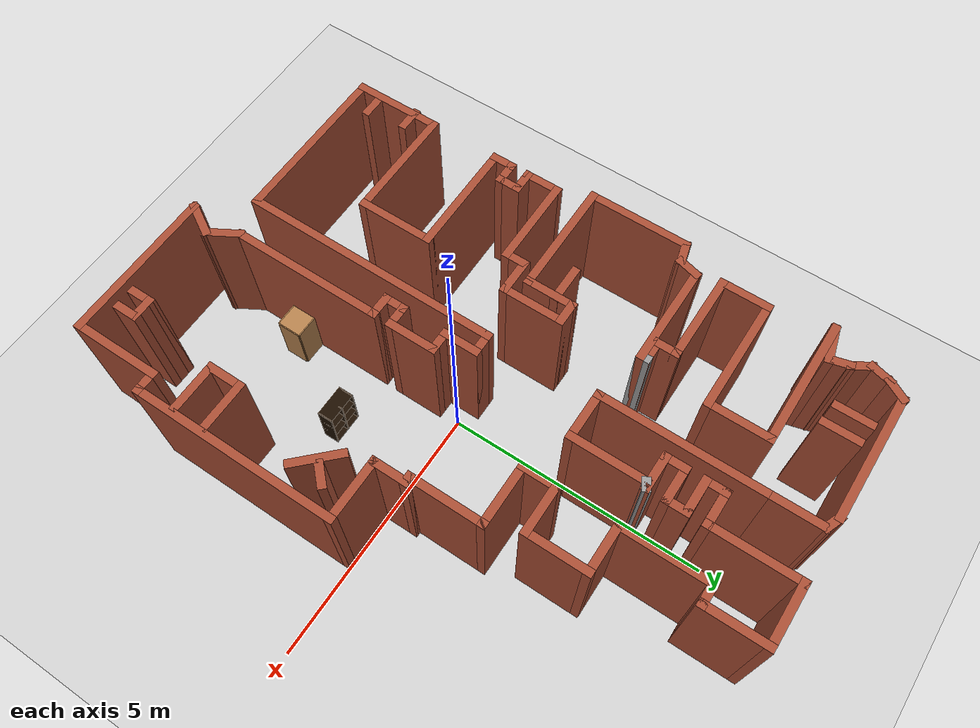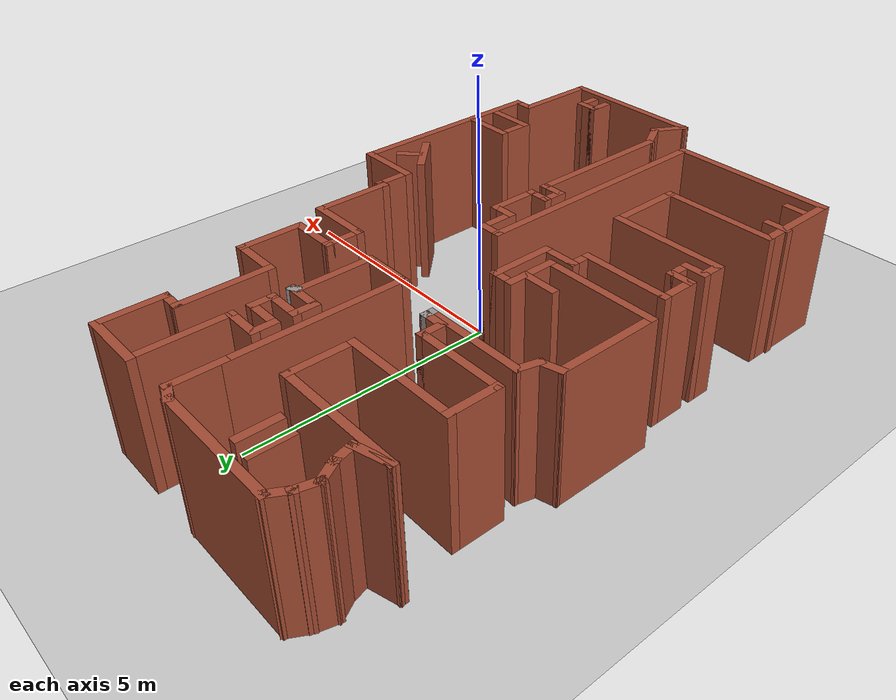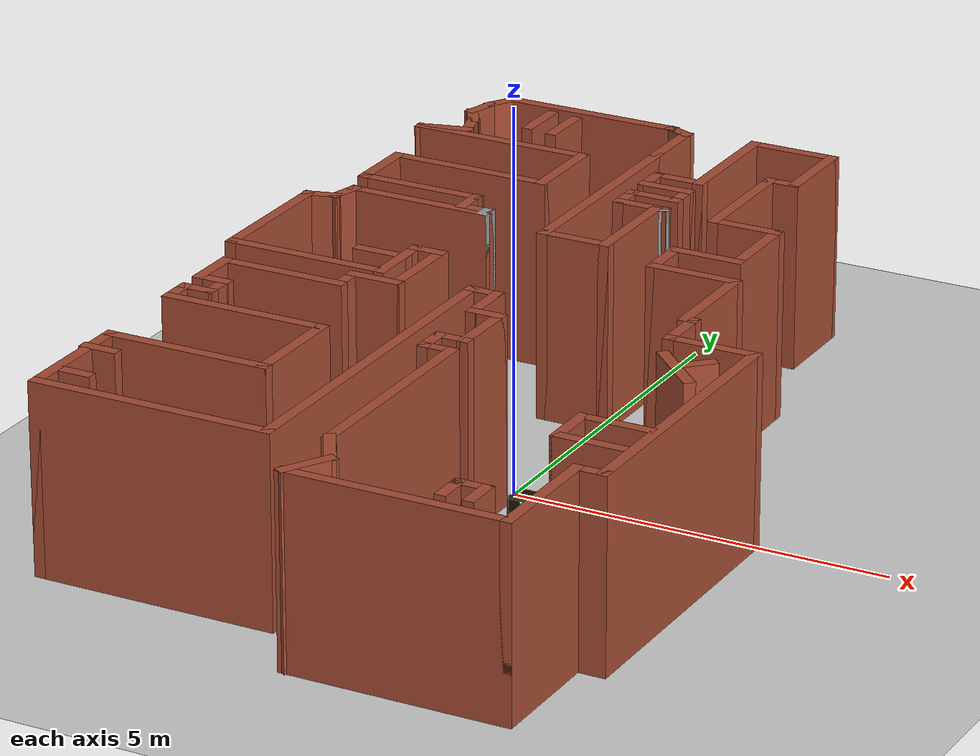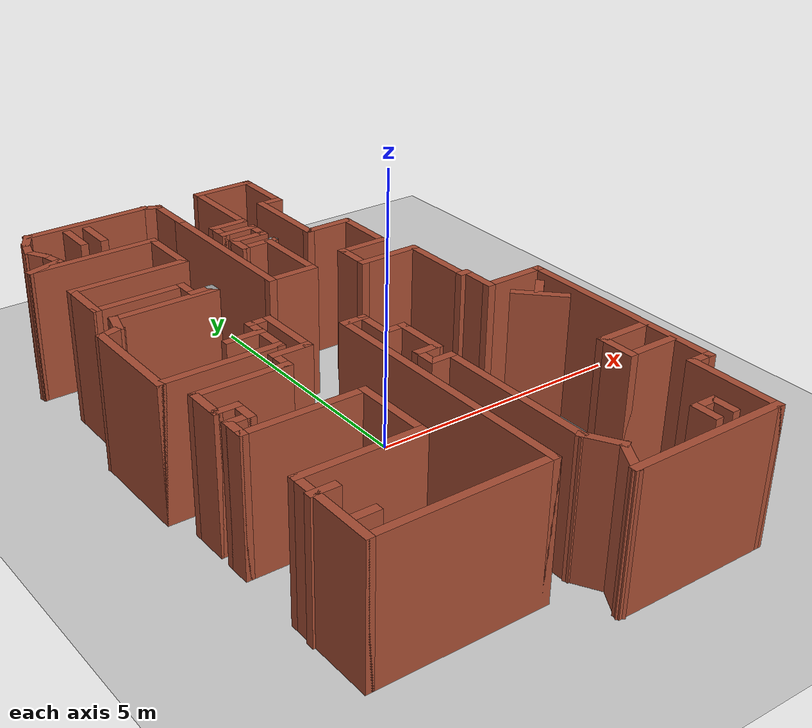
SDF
<sdf version="1.6">
 <world name="default">
  <light name="sun" type="directional">
   <pose>0 0 10 0 -0 0</pose>
   <diffuse>0.8 0.8 0.8 1</diffuse>
   <specular>0.2 0.2 0.2 1</specular>
   <attenuation>
    <range>1000</range>
    <constant>0.9</constant>
    <linear>0.01</linear>
    <quadratic>0.001</quadratic>
   </attenuation>
   <direction>-0.5 0.1 -0.9</direction>
  </light>
  <model name="ground_plane">
   <static>1</static>
   <link name="link">
    <collision name="collision">
     <geometry><plane><normal>0 0 1</normal><size>100 100</size></plane></geometry>
     <surface>
      <contact><collide_bitmask>65535</collide_bitmask></contact>
      <friction><ode><mu>100</mu><mu2>50</mu2></ode></friction>
     </surface>
    </collision>
    <visual name="visual">
     <cast_shadows>0</cast_shadows>
     <geometry><plane><normal>0 0 1</normal><size>100 100</size></plane></geometry>
     <material>
      <script><uri>file://media/materials/scripts/gazebo.material</uri><name>Gazebo/Grey</name></script>
     </material>
    </visual>
   </link>
  </model>
  <gravity>0 0 -9.8</gravity>
  <magnetic_field>6e-06 2.3e-05 -4.2e-05</magnetic_field>
  <atmosphere type="adiabatic"/>
  <physics name="default_physics" default="0" type="ode">
   <max_step_size>0.001</max_step_size>
   <real_time_factor>1</real_time_factor>
   <real_time_update_rate>1000</real_time_update_rate>
  </physics>
  <scene><ambient>0.4 0.4 0.4 1</ambient><background>0.7 0.7 0.7 1</background><shadows>1</shadows></scene>
  <audio><device>default</device></audio>
  <spherical_coordinates>
   <surface_model>EARTH_WGS84</surface_model>
   <latitude_deg>0</latitude_deg>
   <longitude_deg>0</longitude_deg>
   <elevation>0</elevation>
   <heading_deg>0</heading_deg>
  </spherical_coordinates>
  <model name="map_23">
   <pose>-0.42005 0.4067 0 0 -0 0</pose>
   <link name="Wall_10">
    <collision name="Wall_10_Collision">
     <geometry><box><size>0.5 0.15 2.5</size></box></geometry>
     <pose>0 0 1.25 0 -0 0</pose>
    </collision>
    <visual name="Wall_10_Visual">
     <pose>0 0 1.25 0 -0 0</pose>
     <geometry><box><size>0.5 0.15 2.5</size></box></geometry>
     <material>
      <script><uri>file://media/materials/scripts/gazebo.material</uri><name>Gazebo/Bricks</name></script>
      <ambient>1 1 1 1</ambient>
     </material>
     <meta><layer>0</layer></meta>
    </visual>
    <pose>-3.17865 5.43063 0 0 -0 -1.8326</pose>
   </link>
   <link name="Wall_100">
    <collision name="Wall_100_Collision">
     <geometry><box><size>0.426148 0.15 2.5</size></box></geometry>
     <pose>0 0 1.25 0 -0 0</pose>
    </collision>
    <visual name="Wall_100_Visual">
     <pose>0 0 1.25 0 -0 0</pose>
     <geometry><box><size>0.426148 0.15 2.5</size></box></geometry>
     <material>
      <script><uri>file://media/materials/scripts/gazebo.material</uri><name>Gazebo/Bricks</name></script>
      <ambient>1 1 1 1</ambient>
     </material>
     <meta><layer>0</layer></meta>
    </visual>
    <pose>-0.480765 5.85 0 0 -0 2.7494</pose>
   </link>
   <link name="Wall_102">
    <collision name="Wall_102_Collision">
     <geometry><box><size>0.5 0.15 2.5</size></box></geometry>
     <pose>0 0 1.25 0 -0 0</pose>
    </collision>
    <visual name="Wall_102_Visual">
     <pose>0 0 1.25 0 -0 0</pose>
     <geometry><box><size>0.5 0.15 2.5</size></box></geometry>
     <material>
      <script><uri>file://media/materials/scripts/gazebo.material</uri><name>Gazebo/Bricks</name></script>
      <ambient>1 1 1 1</ambient>
     </material>
     <meta><layer>0</layer></meta>
    </visual>
    <pose>2.3061 -5.44127 0 0 -0 1.5708</pose>
   </link>
   <link name="Wall_103">
    <collision name="Wall_103_Collision">
     <geometry><box><size>0.5 0.15 2.5</size></box></geometry>
     <pose>0 0 1.25 0 -0 0</pose>
    </collision>
    <visual name="Wall_103_Visual">
     <pose>0 0 1.25 0 -0 0</pose>
     <geometry><box><size>0.5 0.15 2.5</size></box></geometry>
     <material>
      <script><uri>file://media/materials/scripts/gazebo.material</uri><name>Gazebo/Bricks</name></script>
      <ambient>1 1 1 1</ambient>
     </material>
     <meta><layer>0</layer></meta>
    </visual>
    <pose>2.4811 -5.26627 0 0 -0 0</pose>
   </link>
   <link name="Wall_104">
    <collision name="Wall_104_Collision">
     <geometry><box><size>0.5 0.15 2.5</size></box></geometry>
     <pose>0 0 1.25 0 -0 0</pose>
    </collision>
    <visual name="Wall_104_Visual">
     <pose>0 0 1.25 0 -0 0</pose>
     <geometry><box><size>0.5 0.15 2.5</size></box></geometry>
     <material>
      <script><uri>file://media/materials/scripts/gazebo.material</uri><name>Gazebo/Bricks</name></script>
      <ambient>1 1 1 1</ambient>
     </material>
     <meta><layer>0</layer></meta>
    </visual>
    <pose>2.6561 -5.44127 0 0 -0 -1.5708</pose>
   </link>
   <link name="Wall_106">
    <collision name="Wall_106_Collision">
     <geometry><box><size>1 0.15 2.5</size></box></geometry>
     <pose>0 0 1.25 0 -0 0</pose>
    </collision>
    <visual name="Wall_106_Visual">
     <pose>0 0 1.25 0 -0 0</pose>
     <geometry><box><size>1 0.15 2.5</size></box></geometry>
     <material>
      <script><uri>file://media/materials/scripts/gazebo.material</uri><name>Gazebo/Bricks</name></script>
      <ambient>1 1 1 1</ambient>
     </material>
     <meta><layer>0</layer></meta>
    </visual>
    <pose>3.10702 -3.00251 0 0 -0 3.14159</pose>
   </link>
   <link name="Wall_107">
    <collision name="Wall_107_Collision">
     <geometry><box><size>0.75 0.15 2.5</size></box></geometry>
     <pose>0 0 1.25 0 -0 0</pose>
    </collision>
    <visual name="Wall_107_Visual">
     <pose>0 0 1.25 0 -0 0</pose>
     <geometry><box><size>0.75 0.15 2.5</size></box></geometry>
     <material>
      <script><uri>file://media/materials/scripts/gazebo.material</uri><name>Gazebo/Bricks</name></script>
      <ambient>1 1 1 1</ambient>
     </material>
     <meta><layer>0</layer></meta>
    </visual>
    <pose>2.68202 -3.30251 0 0 -0 -1.5708</pose>
   </link>
   <link name="Wall_108">
    <collision name="Wall_108_Collision">
     <geometry><box><size>1 0.15 2.5</size></box></geometry>
     <pose>0 0 1.25 0 -0 0</pose>
    </collision>
    <visual name="Wall_108_Visual">
     <pose>0 0 1.25 0 -0 0</pose>
     <geometry><box><size>1 0.15 2.5</size></box></geometry>
     <material>
      <script><uri>file://media/materials/scripts/gazebo.material</uri><name>Gazebo/Bricks</name></script>
      <ambient>1 1 1 1</ambient>
     </material>
     <meta><layer>0</layer></meta>
    </visual>
    <pose>3.10702 -3.60251 0 0 -0 0</pose>
   </link>
   <link name="Wall_11">
    <collision name="Wall_11_Collision">
     <geometry><box><size>0.5 0.15 2.5</size></box></geometry>
     <pose>0 0 1.25 0 -0 0</pose>
    </collision>
    <visual name="Wall_11_Visual">
     <pose>0 0 1.25 0 -0 0</pose>
     <geometry><box><size>0.5 0.15 2.5</size></box></geometry>
     <material>
      <script><uri>file://media/materials/scripts/gazebo.material</uri><name>Gazebo/Bricks</name></script>
      <ambient>1 1 1 1</ambient>
     </material>
     <meta><layer>0</layer></meta>
    </visual>
    <pose>-3.13644 5.11004 0 0 -0 -1.0472</pose>
   </link>
   <link name="Wall_110">
    <collision name="Wall_110_Collision">
     <geometry><box><size>0.5 0.15 2.5</size></box></geometry>
     <pose>0 0 1.25 0 -0 0</pose>
    </collision>
    <visual name="Wall_110_Visual">
     <pose>0 0 1.25 0 -0 0</pose>
     <geometry><box><size>0.5 0.15 2.5</size></box></geometry>
     <material>
      <script><uri>file://media/materials/scripts/gazebo.material</uri><name>Gazebo/Bricks</name></script>
      <ambient>1 1 1 1</ambient>
     </material>
     <meta><layer>0</layer></meta>
    </visual>
    <pose>-3.23216 -3.9046 0 0 -0 0</pose>
   </link>
   <link name="Wall_112">
    <collision name="Wall_112_Collision">
     <geometry><box><size>0.5 0.15 2.5</size></box></geometry>
     <pose>0 0 1.25 0 -0 0</pose>
    </collision>
    <visual name="Wall_112_Visual">
     <pose>0 0 1.25 0 -0 0</pose>
     <geometry><box><size>0.5 0.15 2.5</size></box></geometry>
     <material>
      <script><uri>file://media/materials/scripts/gazebo.material</uri><name>Gazebo/Bricks</name></script>
      <ambient>1 1 1 1</ambient>
     </material>
     <meta><layer>0</layer></meta>
    </visual>
    <pose>-3.11651 -4.64478 0 0 -0 0</pose>
   </link>
   <link name="Wall_116">
    <collision name="Wall_116_Collision">
     <geometry><box><size>0.75 0.15 2.5</size></box></geometry>
     <pose>0 0 1.25 0 -0 0</pose>
    </collision>
    <visual name="Wall_116_Visual">
     <pose>0 0 1.25 0 -0 0</pose>
     <geometry><box><size>0.75 0.15 2.5</size></box></geometry>
     <material>
      <script><uri>file://media/materials/scripts/gazebo.material</uri><name>Gazebo/Bricks</name></script>
      <ambient>1 1 1 1</ambient>
     </material>
     <meta><layer>0</layer></meta>
    </visual>
    <pose>-1.81045 0.328298 0 0 -0 3.14159</pose>
   </link>
   <link name="Wall_12">
    <collision name="Wall_12_Collision">
     <geometry><box><size>0.5 0.15 2.5</size></box></geometry>
     <pose>0 0 1.25 0 -0 0</pose>
    </collision>
    <visual name="Wall_12_Visual">
     <pose>0 0 1.25 0 -0 0</pose>
     <geometry><box><size>0.5 0.15 2.5</size></box></geometry>
     <material>
      <script><uri>file://media/materials/scripts/gazebo.material</uri><name>Gazebo/Bricks</name></script>
      <ambient>1 1 1 1</ambient>
     </material>
     <meta><layer>0</layer></meta>
    </visual>
    <pose>-3.00365 4.78944 0 0 -0 -1.309</pose>
   </link>
   <link name="Wall_120">
    <collision name="Wall_120_Collision">
     <geometry><box><size>0.75 0.15 2.5</size></box></geometry>
     <pose>0 0 1.25 0 -0 0</pose>
    </collision>
    <visual name="Wall_120_Visual">
     <pose>0 0 1.25 0 -0 0</pose>
     <geometry><box><size>0.75 0.15 2.5</size></box></geometry>
     <material>
      <script><uri>file://media/materials/scripts/gazebo.material</uri><name>Gazebo/Bricks</name></script>
      <ambient>1 1 1 1</ambient>
     </material>
     <meta><layer>0</layer></meta>
    </visual>
    <pose>-2.27376 5.37147 0 0 -0 -1.5708</pose>
   </link>
   <link name="Wall_122">
    <collision name="Wall_122_Collision">
     <geometry><box><size>0.75 0.15 2.5</size></box></geometry>
     <pose>0 0 1.25 0 -0 0</pose>
    </collision>
    <visual name="Wall_122_Visual">
     <pose>0 0 1.25 0 -0 0</pose>
     <geometry><box><size>0.75 0.15 2.5</size></box></geometry>
     <material>
      <script><uri>file://media/materials/scripts/gazebo.material</uri><name>Gazebo/Bricks</name></script>
      <ambient>1 1 1 1</ambient>
     </material>
     <meta><layer>0</layer></meta>
    </visual>
    <pose>-1.90367 5.32521 0 0 -0 -1.5708</pose>
   </link>
   <link name="Wall_124">
    <collision name="Wall_124_Collision">
     <geometry><box><size>1 0.15 2.5</size></box></geometry>
     <pose>0 0 1.25 0 -0 0</pose>
    </collision>
    <visual name="Wall_124_Visual">
     <pose>0 0 1.25 0 -0 0</pose>
     <geometry><box><size>1 0.15 2.5</size></box></geometry>
     <material>
      <script><uri>file://media/materials/scripts/gazebo.material</uri><name>Gazebo/Bricks</name></script>
      <ambient>1 1 1 1</ambient>
     </material>
     <meta><layer>0</layer></meta>
    </visual>
    <pose>2.98805 -1.22193 0 0 -0 -0.785398</pose>
   </link>
   <link name="Wall_126">
    <collision name="Wall_126_Collision">
     <geometry><box><size>0.5 0.15 2.5</size></box></geometry>
     <pose>0 0 1.25 0 -0 0</pose>
    </collision>
    <visual name="Wall_126_Visual">
     <pose>0 0 1.25 0 -0 0</pose>
     <geometry><box><size>0.5 0.15 2.5</size></box></geometry>
     <material>
      <script><uri>file://media/materials/scripts/gazebo.material</uri><name>Gazebo/Bricks</name></script>
      <ambient>1 1 1 1</ambient>
     </material>
     <meta><layer>0</layer></meta>
    </visual>
    <pose>3.15707 -1.01047 0 0 -0 0.785398</pose>
   </link>
   <link name="Wall_13">
    <collision name="Wall_13_Collision">
     <geometry><box><size>0.75 0.15 2.5</size></box></geometry>
     <pose>0 0 1.25 0 -0 0</pose>
    </collision>
    <visual name="Wall_13_Visual">
     <pose>0 0 1.25 0 -0 0</pose>
     <geometry><box><size>0.75 0.15 2.5</size></box></geometry>
     <material>
      <script><uri>file://media/materials/scripts/gazebo.material</uri><name>Gazebo/Bricks</name></script>
      <ambient>1 1 1 1</ambient>
     </material>
     <meta><layer>0</layer></meta>
    </visual>
    <pose>-3.24813 4.54276 0 0 -0 -2.87979</pose>
   </link>
   <link name="Wall_14">
    <collision name="Wall_14_Collision">
     <geometry><box><size>2.5 0.15 2.5</size></box></geometry>
     <pose>0 0 1.25 0 -0 0</pose>
    </collision>
    <visual name="Wall_14_Visual">
     <pose>0 0 1.25 0 -0 0</pose>
     <geometry><box><size>2.5 0.15 2.5</size></box></geometry>
     <material>
      <script><uri>file://media/materials/scripts/gazebo.material</uri><name>Gazebo/Bricks</name></script>
      <ambient>1 1 1 1</ambient>
     </material>
     <meta><layer>0</layer></meta>
    </visual>
    <pose>-2.36291 4.46512 0 0 -0 0</pose>
   </link>
   <link name="Wall_15">
    <collision name="Wall_15_Collision">
     <geometry><box><size>1.25 0.15 2.5</size></box></geometry>
     <pose>0 0 1.25 0 -0 0</pose>
    </collision>
    <visual name="Wall_15_Visual">
     <pose>0 0 1.25 0 -0 0</pose>
     <geometry><box><size>1.25 0.15 2.5</size></box></geometry>
     <material>
      <script><uri>file://media/materials/scripts/gazebo.material</uri><name>Gazebo/Bricks</name></script>
      <ambient>1 1 1 1</ambient>
     </material>
     <meta><layer>0</layer></meta>
    </visual>
    <pose>-1.18791 3.91512 0 0 -0 -1.5708</pose>
   </link>
   <link name="Wall_16">
    <collision name="Wall_16_Collision">
     <geometry><box><size>2.25 0.15 2.5</size></box></geometry>
     <pose>0 0 1.25 0 -0 0</pose>
    </collision>
    <visual name="Wall_16_Visual">
     <pose>0 0 1.25 0 -0 0</pose>
     <geometry><box><size>2.25 0.15 2.5</size></box></geometry>
     <material>
      <script><uri>file://media/materials/scripts/gazebo.material</uri><name>Gazebo/Bricks</name></script>
      <ambient>1 1 1 1</ambient>
     </material>
     <meta><layer>0</layer></meta>
    </visual>
    <pose>-2.23791 3.36512 0 0 -0 3.14159</pose>
   </link>
   <link name="Wall_19">
    <collision name="Wall_19_Collision">
     <geometry><box><size>1 0.15 2.5</size></box></geometry>
     <pose>0 0 1.25 0 -0 0</pose>
    </collision>
    <visual name="Wall_19_Visual">
     <pose>0 0 1.25 0 -0 0</pose>
     <geometry><box><size>1 0.15 2.5</size></box></geometry>
     <material>
      <script><uri>file://media/materials/scripts/gazebo.material</uri><name>Gazebo/Bricks</name></script>
      <ambient>1 1 1 1</ambient>
     </material>
     <meta><layer>0</layer></meta>
    </visual>
    <pose>-3.28791 2.94012 0 0 -0 -1.5708</pose>
   </link>
   <link name="Wall_20">
    <collision name="Wall_20_Collision">
     <geometry><box><size>1.75 0.15 2.5</size></box></geometry>
     <pose>0 0 1.25 0 -0 0</pose>
    </collision>
    <visual name="Wall_20_Visual">
     <pose>0 0 1.25 0 -0 0</pose>
     <geometry><box><size>1.75 0.15 2.5</size></box></geometry>
     <material>
      <script><uri>file://media/materials/scripts/gazebo.material</uri><name>Gazebo/Bricks</name></script>
      <ambient>1 1 1 1</ambient>
     </material>
     <meta><layer>0</layer></meta>
    </visual>
    <pose>-2.48791 2.51512 0 0 -0 0</pose>
   </link>
   <link name="Wall_21">
    <collision name="Wall_21_Collision">
     <geometry><box><size>0.5 0.15 2.5</size></box></geometry>
     <pose>0 0 1.25 0 -0 0</pose>
    </collision>
    <visual name="Wall_21_Visual">
     <pose>0 0 1.25 0 -0 0</pose>
     <geometry><box><size>0.5 0.15 2.5</size></box></geometry>
     <material>
      <script><uri>file://media/materials/scripts/gazebo.material</uri><name>Gazebo/Bricks</name></script>
      <ambient>1 1 1 1</ambient>
     </material>
     <meta><layer>0</layer></meta>
    </visual>
    <pose>-1.68791 2.34012 0 0 -0 -1.5708</pose>
   </link>
   <link name="Wall_22">
    <collision name="Wall_22_Collision">
     <geometry><box><size>0.5 0.15 2.5</size></box></geometry>
     <pose>0 0 1.25 0 -0 0</pose>
    </collision>
    <visual name="Wall_22_Visual">
     <pose>0 0 1.25 0 -0 0</pose>
     <geometry><box><size>0.5 0.15 2.5</size></box></geometry>
     <material>
      <script><uri>file://media/materials/scripts/gazebo.material</uri><name>Gazebo/Bricks</name></script>
      <ambient>1 1 1 1</ambient>
     </material>
     <meta><layer>0</layer></meta>
    </visual>
    <pose>-1.51291 2.16512 0 0 -0 0</pose>
   </link>
   <link name="Wall_23">
    <collision name="Wall_23_Collision">
     <geometry><box><size>0.25 0.15 2.5</size></box></geometry>
     <pose>0 0 1.25 0 -0 0</pose>
    </collision>
    <visual name="Wall_23_Visual">
     <pose>0 0 1.25 0 -0 0</pose>
     <geometry><box><size>0.25 0.15 2.5</size></box></geometry>
     <material>
      <script><uri>file://media/materials/scripts/gazebo.material</uri><name>Gazebo/Grey</name></script>
      <ambient>1 1 1 1</ambient>
     </material>
     <meta><layer>0</layer></meta>
    </visual>
    <pose>-1.33791 2.11512 0 0 -0 -1.5708</pose>
   </link>
   <link name="Wall_24">
    <collision name="Wall_24_Collision">
     <geometry><box><size>2 0.15 2.5</size></box></geometry>
     <pose>0 0 1.25 0 -0 0</pose>
    </collision>
    <visual name="Wall_24_Visual">
     <pose>0 0 1.25 0 -0 0</pose>
     <geometry><box><size>2 0.15 2.5</size></box></geometry>
     <material>
      <script><uri>file://media/materials/scripts/gazebo.material</uri><name>Gazebo/Bricks</name></script>
      <ambient>1 1 1 1</ambient>
     </material>
     <meta><layer>0</layer></meta>
    </visual>
    <pose>-2.26291 2.06512 0 0 -0 3.14159</pose>
   </link>
   <link name="Wall_25">
    <collision name="Wall_25_Collision">
     <geometry><box><size>0.5 0.15 2.5</size></box></geometry>
     <pose>0 0 1.25 0 -0 0</pose>
    </collision>
    <visual name="Wall_25_Visual">
     <pose>0 0 1.25 0 -0 0</pose>
     <geometry><box><size>0.5 0.15 2.5</size></box></geometry>
     <material>
      <script><uri>file://media/materials/scripts/gazebo.material</uri><name>Gazebo/Bricks</name></script>
      <ambient>1 1 1 1</ambient>
     </material>
     <meta><layer>0</layer></meta>
    </visual>
    <pose>-3.2332 1.89608 0 0 -0 -1.8326</pose>
   </link>
   <link name="Wall_26">
    <collision name="Wall_26_Collision">
     <geometry><box><size>0.5 0.15 2.5</size></box></geometry>
     <pose>0 0 1.25 0 -0 0</pose>
    </collision>
    <visual name="Wall_26_Visual">
     <pose>0 0 1.25 0 -0 0</pose>
     <geometry><box><size>0.5 0.15 2.5</size></box></geometry>
     <material>
      <script><uri>file://media/materials/scripts/gazebo.material</uri><name>Gazebo/Bricks</name></script>
      <ambient>1 1 1 1</ambient>
     </material>
     <meta><layer>0</layer></meta>
    </visual>
    <pose>-3.44753 1.68175 0 0 -0 -2.87979</pose>
   </link>
   <link name="Wall_27">
    <collision name="Wall_27_Collision">
     <geometry><box><size>2 0.15 2.5</size></box></geometry>
     <pose>0 0 1.25 0 -0 0</pose>
    </collision>
    <visual name="Wall_27_Visual">
     <pose>0 0 1.25 0 -0 0</pose>
     <geometry><box><size>2 0.15 2.5</size></box></geometry>
     <material>
      <script><uri>file://media/materials/scripts/gazebo.material</uri><name>Gazebo/Bricks</name></script>
      <ambient>1 1 1 1</ambient>
     </material>
     <meta><layer>0</layer></meta>
    </visual>
    <pose>-3.61657 0.711456 0 0 -0 -1.5708</pose>
   </link>
   <link name="Wall_28">
    <collision name="Wall_28_Collision">
     <geometry><box><size>2.25 0.15 2.5</size></box></geometry>
     <pose>0 0 1.25 0 -0 0</pose>
    </collision>
    <visual name="Wall_28_Visual">
     <pose>0 0 1.25 0 -0 0</pose>
     <geometry><box><size>2.25 0.15 2.5</size></box></geometry>
     <material>
      <script><uri>file://media/materials/scripts/gazebo.material</uri><name>Gazebo/Bricks</name></script>
      <ambient>1 1 1 1</ambient>
     </material>
     <meta><layer>0</layer></meta>
    </visual>
    <pose>-2.56657 -0.213544 0 0 -0 0</pose>
   </link>
   <link name="Wall_29">
    <collision name="Wall_29_Collision">
     <geometry><box><size>1 0.15 2.5</size></box></geometry>
     <pose>0 0 1.25 0 -0 0</pose>
    </collision>
    <visual name="Wall_29_Visual">
     <pose>0 0 1.25 0 -0 0</pose>
     <geometry><box><size>1 0.15 2.5</size></box></geometry>
     <material>
      <script><uri>file://media/materials/scripts/gazebo.material</uri><name>Gazebo/Bricks</name></script>
      <ambient>1 1 1 1</ambient>
     </material>
     <meta><layer>0</layer></meta>
    </visual>
    <pose>-1.51657 0.211456 0 0 -0 1.5708</pose>
   </link>
   <link name="Wall_32">
    <collision name="Wall_32_Collision">
     <geometry><box><size>0.5 0.15 2.5</size></box></geometry>
     <pose>0 0 1.25 0 -0 0</pose>
    </collision>
    <visual name="Wall_32_Visual">
     <pose>0 0 1.25 0 -0 0</pose>
     <geometry><box><size>0.5 0.15 2.5</size></box></geometry>
     <material>
      <script><uri>file://media/materials/scripts/gazebo.material</uri><name>Gazebo/Bricks</name></script>
      <ambient>1 1 1 1</ambient>
     </material>
     <meta><layer>0</layer></meta>
    </visual>
    <pose>-1.34157 0.636456 0 0 -0 0</pose>
   </link>
   <link name="Wall_33">
    <collision name="Wall_33_Collision">
     <geometry><box><size>1.25 0.15 2.5</size></box></geometry>
     <pose>0 0 1.25 0 -0 0</pose>
    </collision>
    <visual name="Wall_33_Visual">
     <pose>0 0 1.25 0 -0 0</pose>
     <geometry><box><size>1.25 0.15 2.5</size></box></geometry>
     <material>
      <script><uri>file://media/materials/scripts/gazebo.material</uri><name>Gazebo/Bricks</name></script>
      <ambient>1 1 1 1</ambient>
     </material>
     <meta><layer>0</layer></meta>
    </visual>
    <pose>-1.16657 0.086456 0 0 -0 -1.5708</pose>
   </link>
   <link name="Wall_34">
    <collision name="Wall_34_Collision">
     <geometry><box><size>0.75 0.15 2.5</size></box></geometry>
     <pose>0 0 1.25 0 -0 0</pose>
    </collision>
    <visual name="Wall_34_Visual">
     <pose>0 0 1.25 0 -0 0</pose>
     <geometry><box><size>0.75 0.15 2.5</size></box></geometry>
     <material>
      <script><uri>file://media/materials/scripts/gazebo.material</uri><name>Gazebo/Bricks</name></script>
      <ambient>1 1 1 1</ambient>
     </material>
     <meta><layer>0</layer></meta>
    </visual>
    <pose>-1.46657 -0.463544 0 0 -0 3.14159</pose>
   </link>
   <link name="Wall_35">
    <collision name="Wall_35_Collision">
     <geometry><box><size>0.5 0.15 2.5</size></box></geometry>
     <pose>0 0 1.25 0 -0 0</pose>
    </collision>
    <visual name="Wall_35_Visual">
     <pose>0 0 1.25 0 -0 0</pose>
     <geometry><box><size>0.5 0.15 2.5</size></box></geometry>
     <material>
      <script><uri>file://media/materials/scripts/gazebo.material</uri><name>Gazebo/Bricks</name></script>
      <ambient>1 1 1 1</ambient>
     </material>
     <meta><layer>0</layer></meta>
    </visual>
    <pose>-1.76657 -0.638544 0 0 -0 -1.5708</pose>
   </link>
   <link name="Wall_36">
    <collision name="Wall_36_Collision">
     <geometry><box><size>1.75 0.15 2.5</size></box></geometry>
     <pose>0 0 1.25 0 -0 0</pose>
    </collision>
    <visual name="Wall_36_Visual">
     <pose>0 0 1.25 0 -0 0</pose>
     <geometry><box><size>1.75 0.15 2.5</size></box></geometry>
     <material>
      <script><uri>file://media/materials/scripts/gazebo.material</uri><name>Gazebo/Bricks</name></script>
      <ambient>1 1 1 1</ambient>
     </material>
     <meta><layer>0</layer></meta>
    </visual>
    <pose>-2.56657 -0.813544 0 0 -0 3.14159</pose>
   </link>
   <link name="Wall_41">
    <collision name="Wall_41_Collision">
     <geometry><box><size>0.75 0.15 2.5</size></box></geometry>
     <pose>0 0 1.25 0 -0 0</pose>
    </collision>
    <visual name="Wall_41_Visual">
     <pose>0 0 1.25 0 -0 0</pose>
     <geometry><box><size>0.75 0.15 2.5</size></box></geometry>
     <material>
      <script><uri>file://media/materials/scripts/gazebo.material</uri><name>Gazebo/Bricks</name></script>
      <ambient>1 1 1 1</ambient>
     </material>
     <meta><layer>0</layer></meta>
    </visual>
    <pose>-3.36657 -1.11354 0 0 -0 -1.5708</pose>
   </link>
   <link name="Wall_42">
    <collision name="Wall_42_Collision">
     <geometry><box><size>0.5 0.15 2.5</size></box></geometry>
     <pose>0 0 1.25 0 -0 0</pose>
    </collision>
    <visual name="Wall_42_Visual">
     <pose>0 0 1.25 0 -0 0</pose>
     <geometry><box><size>0.5 0.15 2.5</size></box></geometry>
     <material>
      <script><uri>file://media/materials/scripts/gazebo.material</uri><name>Gazebo/Bricks</name></script>
      <ambient>1 1 1 1</ambient>
     </material>
     <meta><layer>0</layer></meta>
    </visual>
    <pose>-3.19157 -1.41354 0 0 -0 0</pose>
   </link>
   <link name="Wall_43">
    <collision name="Wall_43_Collision">
     <geometry><box><size>0.5 0.15 2.5</size></box></geometry>
     <pose>0 0 1.25 0 -0 0</pose>
    </collision>
    <visual name="Wall_43_Visual">
     <pose>0 0 1.25 0 -0 0</pose>
     <geometry><box><size>0.5 0.15 2.5</size></box></geometry>
     <material>
      <script><uri>file://media/materials/scripts/gazebo.material</uri><name>Gazebo/Bricks</name></script>
      <ambient>1 1 1 1</ambient>
     </material>
     <meta><layer>0</layer></meta>
    </visual>
    <pose>-3.01657 -1.58854 0 0 -0 -1.5708</pose>
   </link>
   <link name="Wall_44">
    <collision name="Wall_44_Collision">
     <geometry><box><size>0.5 0.15 2.5</size></box></geometry>
     <pose>0 0 1.25 0 -0 0</pose>
    </collision>
    <visual name="Wall_44_Visual">
     <pose>0 0 1.25 0 -0 0</pose>
     <geometry><box><size>0.5 0.15 2.5</size></box></geometry>
     <material>
      <script><uri>file://media/materials/scripts/gazebo.material</uri><name>Gazebo/Bricks</name></script>
      <ambient>1 1 1 1</ambient>
     </material>
     <meta><layer>0</layer></meta>
    </visual>
    <pose>-3.19157 -1.76354 0 0 -0 3.14159</pose>
   </link>
   <link name="Wall_45">
    <collision name="Wall_45_Collision">
     <geometry><box><size>0.5 0.15 2.5</size></box></geometry>
     <pose>0 0 1.25 0 -0 0</pose>
    </collision>
    <visual name="Wall_45_Visual">
     <pose>0 0 1.25 0 -0 0</pose>
     <geometry><box><size>0.5 0.15 2.5</size></box></geometry>
     <material>
      <script><uri>file://media/materials/scripts/gazebo.material</uri><name>Gazebo/Bricks</name></script>
      <ambient>1 1 1 1</ambient>
     </material>
     <meta><layer>0</layer></meta>
    </visual>
    <pose>-3.36657 -1.93854 0 0 -0 -1.5708</pose>
   </link>
   <link name="Wall_46">
    <collision name="Wall_46_Collision">
     <geometry><box><size>2.25 0.15 2.5</size></box></geometry>
     <pose>0 0 1.25 0 -0 0</pose>
    </collision>
    <visual name="Wall_46_Visual">
     <pose>0 0 1.25 0 -0 0</pose>
     <geometry><box><size>2.25 0.15 2.5</size></box></geometry>
     <material>
      <script><uri>file://media/materials/scripts/gazebo.material</uri><name>Gazebo/Bricks</name></script>
      <ambient>1 1 1 1</ambient>
     </material>
     <meta><layer>0</layer></meta>
    </visual>
    <pose>-2.31657 -2.11354 0 0 -0 0</pose>
   </link>
   <link name="Wall_47">
    <collision name="Wall_47_Collision">
     <geometry><box><size>1.5 0.15 2.5</size></box></geometry>
     <pose>0 0 1.25 0 -0 0</pose>
    </collision>
    <visual name="Wall_47_Visual">
     <pose>0 0 1.25 0 -0 0</pose>
     <geometry><box><size>1.5 0.15 2.5</size></box></geometry>
     <material>
      <script><uri>file://media/materials/scripts/gazebo.material</uri><name>Gazebo/Bricks</name></script>
      <ambient>1 1 1 1</ambient>
     </material>
     <meta><layer>0</layer></meta>
    </visual>
    <pose>-1.26657 -2.78854 0 0 -0 -1.5708</pose>
   </link>
   <link name="Wall_48">
    <collision name="Wall_48_Collision">
     <geometry><box><size>2.25 0.15 2.5</size></box></geometry>
     <pose>0 0 1.25 0 -0 0</pose>
    </collision>
    <visual name="Wall_48_Visual">
     <pose>0 0 1.25 0 -0 0</pose>
     <geometry><box><size>2.25 0.15 2.5</size></box></geometry>
     <material>
      <script><uri>file://media/materials/scripts/gazebo.material</uri><name>Gazebo/Bricks</name></script>
      <ambient>1 1 1 1</ambient>
     </material>
     <meta><layer>0</layer></meta>
    </visual>
    <pose>-2.31657 -3.46354 0 0 -0 3.14159</pose>
   </link>
   <link name="Wall_49">
    <collision name="Wall_49_Collision">
     <geometry><box><size>1.75 0.15 2.5</size></box></geometry>
     <pose>0 0 1.25 0 -0 0</pose>
    </collision>
    <visual name="Wall_49_Visual">
     <pose>0 0 1.25 0 -0 0</pose>
     <geometry><box><size>1.75 0.15 2.5</size></box></geometry>
     <material>
      <script><uri>file://media/materials/scripts/gazebo.material</uri><name>Gazebo/Bricks</name></script>
      <ambient>1 1 1 1</ambient>
     </material>
     <meta><layer>0</layer></meta>
    </visual>
    <pose>-3.36657 -4.26354 0 0 -0 -1.5708</pose>
   </link>
   <link name="Wall_50">
    <collision name="Wall_50_Collision">
     <geometry><box><size>3.25 0.15 2.5</size></box></geometry>
     <pose>0 0 1.25 0 -0 0</pose>
    </collision>
    <visual name="Wall_50_Visual">
     <pose>0 0 1.25 0 -0 0</pose>
     <geometry><box><size>3.25 0.15 2.5</size></box></geometry>
     <material>
      <script><uri>file://media/materials/scripts/gazebo.material</uri><name>Gazebo/Bricks</name></script>
      <ambient>1 1 1 1</ambient>
     </material>
     <meta><layer>0</layer></meta>
    </visual>
    <pose>-1.81657 -5.06354 0 0 -0 0</pose>
   </link>
   <link name="Wall_51">
    <collision name="Wall_51_Collision">
     <geometry><box><size>5 0.15 2.5</size></box></geometry>
     <pose>0 0 1.25 0 -0 0</pose>
    </collision>
    <visual name="Wall_51_Visual">
     <pose>0 0 1.25 0 -0 0</pose>
     <geometry><box><size>5 0.15 2.5</size></box></geometry>
     <material>
      <script><uri>file://media/materials/scripts/gazebo.material</uri><name>Gazebo/Bricks</name></script>
      <ambient>1 1 1 1</ambient>
     </material>
     <meta><layer>0</layer></meta>
    </visual>
    <pose>-0.266572 -2.63854 0 0 -0 1.5708</pose>
   </link>
   <link name="Wall_52">
    <collision name="Wall_52_Collision">
     <geometry><box><size>0.5 0.15 2.5</size></box></geometry>
     <pose>0 0 1.25 0 -0 0</pose>
    </collision>
    <visual name="Wall_52_Visual">
     <pose>0 0 1.25 0 -0 0</pose>
     <geometry><box><size>0.5 0.15 2.5</size></box></geometry>
     <material>
      <script><uri>file://media/materials/scripts/gazebo.material</uri><name>Gazebo/Bricks</name></script>
      <ambient>1 1 1 1</ambient>
     </material>
     <meta><layer>0</layer></meta>
    </visual>
    <pose>-0.091572 -0.213544 0 0 -0 0</pose>
   </link>
   <link name="Wall_53">
    <collision name="Wall_53_Collision">
     <geometry><box><size>0.75 0.15 2.5</size></box></geometry>
     <pose>0 0 1.25 0 -0 0</pose>
    </collision>
    <visual name="Wall_53_Visual">
     <pose>0 0 1.25 0 -0 0</pose>
     <geometry><box><size>0.75 0.15 2.5</size></box></geometry>
     <material>
      <script><uri>file://media/materials/scripts/gazebo.material</uri><name>Gazebo/Bricks</name></script>
      <ambient>1 1 1 1</ambient>
     </material>
     <meta><layer>0</layer></meta>
    </visual>
    <pose>0.083428 -0.513544 0 0 -0 -1.5708</pose>
   </link>
   <link name="Wall_54">
    <collision name="Wall_54_Collision">
     <geometry><box><size>0.5 0.15 2.5</size></box></geometry>
     <pose>0 0 1.25 0 -0 0</pose>
    </collision>
    <visual name="Wall_54_Visual">
     <pose>0 0 1.25 0 -0 0</pose>
     <geometry><box><size>0.5 0.15 2.5</size></box></geometry>
     <material>
      <script><uri>file://media/materials/scripts/gazebo.material</uri><name>Gazebo/Bricks</name></script>
      <ambient>1 1 1 1</ambient>
     </material>
     <meta><layer>0</layer></meta>
    </visual>
    <pose>0.258428 -0.813544 0 0 -0 0</pose>
   </link>
   <link name="Wall_55">
    <collision name="Wall_55_Collision">
     <geometry><box><size>1 0.15 2.5</size></box></geometry>
     <pose>0 0 1.25 0 -0 0</pose>
    </collision>
    <visual name="Wall_55_Visual">
     <pose>0 0 1.25 0 -0 0</pose>
     <geometry><box><size>1 0.15 2.5</size></box></geometry>
     <material>
      <script><uri>file://media/materials/scripts/gazebo.material</uri><name>Gazebo/Bricks</name></script>
      <ambient>1 1 1 1</ambient>
     </material>
     <meta><layer>0</layer></meta>
    </visual>
    <pose>0.433428 -1.23854 0 0 -0 -1.5708</pose>
   </link>
   <link name="Wall_56">
    <collision name="Wall_56_Collision">
     <geometry><box><size>0.5 0.15 2.5</size></box></geometry>
     <pose>0 0 1.25 0 -0 0</pose>
    </collision>
    <visual name="Wall_56_Visual">
     <pose>0 0 1.25 0 -0 0</pose>
     <geometry><box><size>0.5 0.15 2.5</size></box></geometry>
     <material>
      <script><uri>file://media/materials/scripts/gazebo.material</uri><name>Gazebo/Bricks</name></script>
      <ambient>1 1 1 1</ambient>
     </material>
     <meta><layer>0</layer></meta>
    </visual>
    <pose>0.258428 -1.66354 0 0 -0 3.14159</pose>
   </link>
   <link name="Wall_57">
    <collision name="Wall_57_Collision">
     <geometry><box><size>0.5 0.15 2.5</size></box></geometry>
     <pose>0 0 1.25 0 -0 0</pose>
    </collision>
    <visual name="Wall_57_Visual">
     <pose>0 0 1.25 0 -0 0</pose>
     <geometry><box><size>0.5 0.15 2.5</size></box></geometry>
     <material>
      <script><uri>file://media/materials/scripts/gazebo.material</uri><name>Gazebo/Bricks</name></script>
      <ambient>1 1 1 1</ambient>
     </material>
     <meta><layer>0</layer></meta>
    </visual>
    <pose>0.083428 -1.83854 0 0 -0 -1.5708</pose>
   </link>
   <link name="Wall_58">
    <collision name="Wall_58_Collision">
     <geometry><box><size>0.5 0.15 2.5</size></box></geometry>
     <pose>0 0 1.25 0 -0 0</pose>
    </collision>
    <visual name="Wall_58_Visual">
     <pose>0 0 1.25 0 -0 0</pose>
     <geometry><box><size>0.5 0.15 2.5</size></box></geometry>
     <material>
      <script><uri>file://media/materials/scripts/gazebo.material</uri><name>Gazebo/Bricks</name></script>
      <ambient>1 1 1 1</ambient>
     </material>
     <meta><layer>0</layer></meta>
    </visual>
    <pose>0.258428 -2.01354 0 0 -0 0</pose>
   </link>
   <link name="Wall_59">
    <collision name="Wall_59_Collision">
     <geometry><box><size>3 0.15 2.5</size></box></geometry>
     <pose>0 0 1.25 0 -0 0</pose>
    </collision>
    <visual name="Wall_59_Visual">
     <pose>0 0 1.25 0 -0 0</pose>
     <geometry><box><size>3 0.15 2.5</size></box></geometry>
     <material>
      <script><uri>file://media/materials/scripts/gazebo.material</uri><name>Gazebo/Bricks</name></script>
      <ambient>1 1 1 1</ambient>
     </material>
     <meta><layer>0</layer></meta>
    </visual>
    <pose>0.433428 -3.43854 0 0 -0 -1.5708</pose>
   </link>
   <link name="Wall_60">
    <collision name="Wall_60_Collision">
     <geometry><box><size>0.75 0.15 2.5</size></box></geometry>
     <pose>0 0 1.25 0 -0 0</pose>
    </collision>
    <visual name="Wall_60_Visual">
     <pose>0 0 1.25 0 -0 0</pose>
     <geometry><box><size>0.75 0.15 2.5</size></box></geometry>
     <material>
      <script><uri>file://media/materials/scripts/gazebo.material</uri><name>Gazebo/Bricks</name></script>
      <ambient>1 1 1 1</ambient>
     </material>
     <meta><layer>0</layer></meta>
    </visual>
    <pose>0.583428 -5.12335 0 0 -0 -1.0472</pose>
   </link>
   <link name="Wall_61">
    <collision name="Wall_61_Collision">
     <geometry><box><size>0.75 0.15 2.5</size></box></geometry>
     <pose>0 0 1.25 0 -0 0</pose>
    </collision>
    <visual name="Wall_61_Visual">
     <pose>0 0 1.25 0 -0 0</pose>
     <geometry><box><size>0.75 0.15 2.5</size></box></geometry>
     <material>
      <script><uri>file://media/materials/scripts/gazebo.material</uri><name>Gazebo/Bricks</name></script>
      <ambient>1 1 1 1</ambient>
     </material>
     <meta><layer>0</layer></meta>
    </visual>
    <pose>0.583428 -5.64297 0 0 -0 -2.0944</pose>
   </link>
   <link name="Wall_62">
    <collision name="Wall_62_Collision">
     <geometry><box><size>3 0.15 2.5</size></box></geometry>
     <pose>0 0 1.25 0 -0 0</pose>
    </collision>
    <visual name="Wall_62_Visual">
     <pose>0 0 1.25 0 -0 0</pose>
     <geometry><box><size>3 0.15 2.5</size></box></geometry>
     <material>
      <script><uri>file://media/materials/scripts/gazebo.material</uri><name>Gazebo/Bricks</name></script>
      <ambient>1 1 1 1</ambient>
     </material>
     <meta><layer>0</layer></meta>
    </visual>
    <pose>1.85843 -5.90277 0 0 -0 0</pose>
   </link>
   <link name="Wall_63">
    <collision name="Wall_63_Collision">
     <geometry><box><size>1.75 0.15 2.5</size></box></geometry>
     <pose>0 0 1.25 0 -0 0</pose>
    </collision>
    <visual name="Wall_63_Visual">
     <pose>0 0 1.25 0 -0 0</pose>
     <geometry><box><size>1.75 0.15 2.5</size></box></geometry>
     <material>
      <script><uri>file://media/materials/scripts/gazebo.material</uri><name>Gazebo/Bricks</name></script>
      <ambient>1 1 1 1</ambient>
     </material>
     <meta><layer>0</layer></meta>
    </visual>
    <pose>3.28343 -5.10277 0 0 -0 1.5708</pose>
   </link>
   <link name="Wall_66">
    <collision name="Wall_66_Collision">
     <geometry><box><size>0.5 0.15 2.5</size></box></geometry>
     <pose>0 0 1.25 0 -0 0</pose>
    </collision>
    <visual name="Wall_66_Visual">
     <pose>0 0 1.25 0 -0 0</pose>
     <geometry><box><size>0.5 0.15 2.5</size></box></geometry>
     <material>
      <script><uri>file://media/materials/scripts/gazebo.material</uri><name>Gazebo/Bricks</name></script>
      <ambient>1 1 1 1</ambient>
     </material>
     <meta><layer>0</layer></meta>
    </visual>
    <pose>3.45843 -4.30277 0 0 -0 0</pose>
   </link>
   <link name="Wall_67">
    <collision name="Wall_67_Collision">
     <geometry><box><size>4 0.15 2.5</size></box></geometry>
     <pose>0 0 1.25 0 -0 0</pose>
    </collision>
    <visual name="Wall_67_Visual">
     <pose>0 0 1.25 0 -0 0</pose>
     <geometry><box><size>4 0.15 2.5</size></box></geometry>
     <material>
      <script><uri>file://media/materials/scripts/gazebo.material</uri><name>Gazebo/Bricks</name></script>
      <ambient>1 1 1 1</ambient>
     </material>
     <meta><layer>0</layer></meta>
    </visual>
    <pose>3.63343 -2.37777 0 0 -0 1.5708</pose>
   </link>
   <link name="Wall_68">
    <collision name="Wall_68_Collision">
     <geometry><box><size>1.25 0.15 2.5</size></box></geometry>
     <pose>0 0 1.25 0 -0 0</pose>
    </collision>
    <visual name="Wall_68_Visual">
     <pose>0 0 1.25 0 -0 0</pose>
     <geometry><box><size>1.25 0.15 2.5</size></box></geometry>
     <material>
      <script><uri>file://media/materials/scripts/gazebo.material</uri><name>Gazebo/Bricks</name></script>
      <ambient>1 1 1 1</ambient>
     </material>
     <meta><layer>0</layer></meta>
    </visual>
    <pose>3.08343 -0.452774 0 0 -0 3.14159</pose>
   </link>
   <link name="Wall_69">
    <collision name="Wall_69_Collision">
     <geometry><box><size>0.75 0.15 2.5</size></box></geometry>
     <pose>0 0 1.25 0 -0 0</pose>
    </collision>
    <visual name="Wall_69_Visual">
     <pose>0 0 1.25 0 -0 0</pose>
     <geometry><box><size>0.75 0.15 2.5</size></box></geometry>
     <material>
      <script><uri>file://media/materials/scripts/gazebo.material</uri><name>Gazebo/Bricks</name></script>
      <ambient>1 1 1 1</ambient>
     </material>
     <meta><layer>0</layer></meta>
    </visual>
    <pose>2.53343 -0.152774 0 0 -0 1.5708</pose>
   </link>
   <link name="Wall_70">
    <collision name="Wall_70_Collision">
     <geometry><box><size>0.25 0.15 2.5</size></box></geometry>
     <pose>0 0 1.25 0 -0 0</pose>
    </collision>
    <visual name="Wall_70_Visual">
     <pose>0 0 1.25 0 -0 0</pose>
     <geometry><box><size>0.25 0.15 2.5</size></box></geometry>
     <material>
      <script><uri>file://media/materials/scripts/gazebo.material</uri><name>Gazebo/Bricks</name></script>
      <ambient>1 1 1 1</ambient>
     </material>
     <meta><layer>0</layer></meta>
    </visual>
    <pose>2.48343 0.147226 0 0 -0 3.14159</pose>
   </link>
   <link name="Wall_71">
    <collision name="Wall_71_Collision">
     <geometry><box><size>1.5 0.15 2.5</size></box></geometry>
     <pose>0 0 1.25 0 -0 0</pose>
    </collision>
    <visual name="Wall_71_Visual">
     <pose>0 0 1.25 0 -0 0</pose>
     <geometry><box><size>1.5 0.15 2.5</size></box></geometry>
     <material>
      <script><uri>file://media/materials/scripts/gazebo.material</uri><name>Gazebo/Bricks</name></script>
      <ambient>1 1 1 1</ambient>
     </material>
     <meta><layer>0</layer></meta>
    </visual>
    <pose>2.43343 0.822226 0 0 -0 1.5708</pose>
   </link>
   <link name="Wall_72">
    <collision name="Wall_72_Collision">
     <geometry><box><size>1.25 0.15 2.5</size></box></geometry>
     <pose>0 0 1.25 0 -0 0</pose>
    </collision>
    <visual name="Wall_72_Visual">
     <pose>0 0 1.25 0 -0 0</pose>
     <geometry><box><size>1.25 0.15 2.5</size></box></geometry>
     <material>
      <script><uri>file://media/materials/scripts/gazebo.material</uri><name>Gazebo/Bricks</name></script>
      <ambient>1 1 1 1</ambient>
     </material>
     <meta><layer>0</layer></meta>
    </visual>
    <pose>1.88343 1.49723 0 0 -0 3.14159</pose>
   </link>
   <link name="Wall_73">
    <collision name="Wall_73_Collision">
     <geometry><box><size>0.75 0.15 2.5</size></box></geometry>
     <pose>0 0 1.25 0 -0 0</pose>
    </collision>
    <visual name="Wall_73_Visual">
     <pose>0 0 1.25 0 -0 0</pose>
     <geometry><box><size>0.75 0.15 2.5</size></box></geometry>
     <material>
      <script><uri>file://media/materials/scripts/gazebo.material</uri><name>Gazebo/Bricks</name></script>
      <ambient>1 1 1 1</ambient>
     </material>
     <meta><layer>0</layer></meta>
    </visual>
    <pose>1.33343 1.79723 0 0 -0 1.5708</pose>
   </link>
   <link name="Wall_74">
    <collision name="Wall_74_Collision">
     <geometry><box><size>1 0.15 2.5</size></box></geometry>
     <pose>0 0 1.25 0 -0 0</pose>
    </collision>
    <visual name="Wall_74_Visual">
     <pose>0 0 1.25 0 -0 0</pose>
     <geometry><box><size>1 0.15 2.5</size></box></geometry>
     <material>
      <script><uri>file://media/materials/scripts/gazebo.material</uri><name>Gazebo/Bricks</name></script>
      <ambient>1 1 1 1</ambient>
     </material>
     <meta><layer>0</layer></meta>
    </visual>
    <pose>1.75843 2.09723 0 0 -0 0</pose>
   </link>
   <link name="Wall_75">
    <collision name="Wall_75_Collision">
     <geometry><box><size>1.25 0.15 2.5</size></box></geometry>
     <pose>0 0 1.25 0 -0 0</pose>
    </collision>
    <visual name="Wall_75_Visual">
     <pose>0 0 1.25 0 -0 0</pose>
     <geometry><box><size>1.25 0.15 2.5</size></box></geometry>
     <material>
      <script><uri>file://media/materials/scripts/gazebo.material</uri><name>Gazebo/Bricks</name></script>
      <ambient>1 1 1 1</ambient>
     </material>
     <meta><layer>0</layer></meta>
    </visual>
    <pose>2.18343 2.64723 0 0 -0 1.5708</pose>
   </link>
   <link name="Wall_78">
    <collision name="Wall_78_Collision">
     <geometry><box><size>1 0.15 2.5</size></box></geometry>
     <pose>0 0 1.25 0 -0 0</pose>
    </collision>
    <visual name="Wall_78_Visual">
     <pose>0 0 1.25 0 -0 0</pose>
     <geometry><box><size>1 0.15 2.5</size></box></geometry>
     <material>
      <script><uri>file://media/materials/scripts/gazebo.material</uri><name>Gazebo/Bricks</name></script>
      <ambient>1 1 1 1</ambient>
     </material>
     <meta><layer>0</layer></meta>
    </visual>
    <pose>1.75843 3.19723 0 0 -0 3.14159</pose>
   </link>
   <link name="Wall_79">
    <collision name="Wall_79_Collision">
     <geometry><box><size>1.75 0.15 2.5</size></box></geometry>
     <pose>0 0 1.25 0 -0 0</pose>
    </collision>
    <visual name="Wall_79_Visual">
     <pose>0 0 1.25 0 -0 0</pose>
     <geometry><box><size>1.75 0.15 2.5</size></box></geometry>
     <material>
      <script><uri>file://media/materials/scripts/gazebo.material</uri><name>Gazebo/Bricks</name></script>
      <ambient>1 1 1 1</ambient>
     </material>
     <meta><layer>0</layer></meta>
    </visual>
    <pose>1.33343 3.99723 0 0 -0 1.5708</pose>
   </link>
   <link name="Wall_8">
    <collision name="Wall_8_Collision">
     <geometry><box><size>2.5 0.15 2.5</size></box></geometry>
     <pose>0 0 1.25 0 -0 0</pose>
    </collision>
    <visual name="Wall_8_Visual">
     <pose>0 0 1.25 0 -0 0</pose>
     <geometry><box><size>2.5 0.15 2.5</size></box></geometry>
     <material>
      <script><uri>file://media/materials/scripts/gazebo.material</uri><name>Gazebo/Bricks</name></script>
      <ambient>1 1 1 1</ambient>
     </material>
     <meta><layer>0</layer></meta>
    </visual>
    <pose>-1.78336 5.90277 0 0 -0 3.14159</pose>
   </link>
   <link name="Wall_80">
    <collision name="Wall_80_Collision">
     <geometry><box><size>0.5 0.15 2.5</size></box></geometry>
     <pose>0 0 1.25 0 -0 0</pose>
    </collision>
    <visual name="Wall_80_Visual">
     <pose>0 0 1.25 0 -0 0</pose>
     <geometry><box><size>0.5 0.15 2.5</size></box></geometry>
     <material>
      <script><uri>file://media/materials/scripts/gazebo.material</uri><name>Gazebo/Bricks</name></script>
      <ambient>1 1 1 1</ambient>
     </material>
     <meta><layer>0</layer></meta>
    </visual>
    <pose>1.50843 4.79723 0 0 -0 0</pose>
   </link>
   <link name="Wall_81">
    <collision name="Wall_81_Collision">
     <geometry><box><size>1.25 0.15 2.5</size></box></geometry>
     <pose>0 0 1.25 0 -0 0</pose>
    </collision>
    <visual name="Wall_81_Visual">
     <pose>0 0 1.25 0 -0 0</pose>
     <geometry><box><size>1.25 0.15 2.5</size></box></geometry>
     <material>
      <script><uri>file://media/materials/scripts/gazebo.material</uri><name>Gazebo/Bricks</name></script>
      <ambient>1 1 1 1</ambient>
     </material>
     <meta><layer>0</layer></meta>
    </visual>
    <pose>1.68343 5.34723 0 0 -0 1.5708</pose>
   </link>
   <link name="Wall_82">
    <collision name="Wall_82_Collision">
     <geometry><box><size>1.25 0.15 2.5</size></box></geometry>
     <pose>0 0 1.25 0 -0 0</pose>
    </collision>
    <visual name="Wall_82_Visual">
     <pose>0 0 1.25 0 -0 0</pose>
     <geometry><box><size>1.25 0.15 2.5</size></box></geometry>
     <material>
      <script><uri>file://media/materials/scripts/gazebo.material</uri><name>Gazebo/Bricks</name></script>
      <ambient>1 1 1 1</ambient>
     </material>
     <meta><layer>0</layer></meta>
    </visual>
    <pose>1.13343 5.89723 0 0 -0 3.14159</pose>
   </link>
   <link name="Wall_83">
    <collision name="Wall_83_Collision">
     <geometry><box><size>1.75 0.15 2.5</size></box></geometry>
     <pose>0 0 1.25 0 -0 0</pose>
    </collision>
    <visual name="Wall_83_Visual">
     <pose>0 0 1.25 0 -0 0</pose>
     <geometry><box><size>1.75 0.15 2.5</size></box></geometry>
     <material>
      <script><uri>file://media/materials/scripts/gazebo.material</uri><name>Gazebo/Bricks</name></script>
      <ambient>1 1 1 1</ambient>
     </material>
     <meta><layer>0</layer></meta>
    </visual>
    <pose>0.583428 5.09723 0 0 -0 -1.5708</pose>
   </link>
   <link name="Wall_84">
    <collision name="Wall_84_Collision">
     <geometry><box><size>0.75 0.15 2.5</size></box></geometry>
     <pose>0 0 1.25 0 -0 0</pose>
    </collision>
    <visual name="Wall_84_Visual">
     <pose>0 0 1.25 0 -0 0</pose>
     <geometry><box><size>0.75 0.15 2.5</size></box></geometry>
     <material>
      <script><uri>file://media/materials/scripts/gazebo.material</uri><name>Gazebo/Bricks</name></script>
      <ambient>1 1 1 1</ambient>
     </material>
     <meta><layer>0</layer></meta>
    </visual>
    <pose>0.283428 4.29723 0 0 -0 3.14159</pose>
   </link>
   <link name="Wall_85">
    <collision name="Wall_85_Collision">
     <geometry><box><size>0.5 0.15 2.5</size></box></geometry>
     <pose>0 0 1.25 0 -0 0</pose>
    </collision>
    <visual name="Wall_85_Visual">
     <pose>0 0 1.25 0 -0 0</pose>
     <geometry><box><size>0.5 0.15 2.5</size></box></geometry>
     <material>
      <script><uri>file://media/materials/scripts/gazebo.material</uri><name>Gazebo/Bricks</name></script>
      <ambient>1 1 1 1</ambient>
     </material>
     <meta><layer>0</layer></meta>
    </visual>
    <pose>-0.016572 4.12223 0 0 -0 -1.5708</pose>
   </link>
   <link name="Wall_86">
    <collision name="Wall_86_Collision">
     <geometry><box><size>0.75 0.15 2.5</size></box></geometry>
     <pose>0 0 1.25 0 -0 0</pose>
    </collision>
    <visual name="Wall_86_Visual">
     <pose>0 0 1.25 0 -0 0</pose>
     <geometry><box><size>0.75 0.15 2.5</size></box></geometry>
     <material>
      <script><uri>file://media/materials/scripts/gazebo.material</uri><name>Gazebo/Bricks</name></script>
      <ambient>1 1 1 1</ambient>
     </material>
     <meta><layer>0</layer></meta>
    </visual>
    <pose>0.283428 3.94723 0 0 -0 0</pose>
   </link>
   <link name="Wall_87">
    <collision name="Wall_87_Collision">
     <geometry><box><size>0.5 0.15 2.5</size></box></geometry>
     <pose>0 0 1.25 0 -0 0</pose>
    </collision>
    <visual name="Wall_87_Visual">
     <pose>0 0 1.25 0 -0 0</pose>
     <geometry><box><size>0.5 0.15 2.5</size></box></geometry>
     <material>
      <script><uri>file://media/materials/scripts/gazebo.material</uri><name>Gazebo/Bricks</name></script>
      <ambient>1 1 1 1</ambient>
     </material>
     <meta><layer>0</layer></meta>
    </visual>
    <pose>0.583428 3.77223 0 0 -0 -1.5708</pose>
   </link>
   <link name="Wall_9">
    <collision name="Wall_9_Collision">
     <geometry><box><size>0.5 0.15 2.5</size></box></geometry>
     <pose>0 0 1.25 0 -0 0</pose>
    </collision>
    <visual name="Wall_9_Visual">
     <pose>0 0 1.25 0 -0 0</pose>
     <geometry><box><size>0.5 0.15 2.5</size></box></geometry>
     <material>
      <script><uri>file://media/materials/scripts/gazebo.material</uri><name>Gazebo/Bricks</name></script>
      <ambient>1 1 1 1</ambient>
     </material>
     <meta><layer>0</layer></meta>
    </visual>
    <pose>-3.04586 5.75122 0 0 -0 -2.0944</pose>
   </link>
   <link name="Wall_92">
    <collision name="Wall_92_Collision">
     <geometry><box><size>0.75 0.15 2.5</size></box></geometry>
     <pose>0 0 1.25 0 -0 0</pose>
    </collision>
    <visual name="Wall_92_Visual">
     <pose>0 0 1.25 0 -0 0</pose>
     <geometry><box><size>0.75 0.15 2.5</size></box></geometry>
     <material>
      <script><uri>file://media/materials/scripts/gazebo.material</uri><name>Gazebo/Bricks</name></script>
      <ambient>1 1 1 1</ambient>
     </material>
     <meta><layer>0</layer></meta>
    </visual>
    <pose>0.283428 3.59723 0 0 -0 3.14159</pose>
   </link>
   <link name="Wall_93">
    <collision name="Wall_93_Collision">
     <geometry><box><size>0.5 0.15 2.5</size></box></geometry>
     <pose>0 0 1.25 0 -0 0</pose>
    </collision>
    <visual name="Wall_93_Visual">
     <pose>0 0 1.25 0 -0 0</pose>
     <geometry><box><size>0.5 0.15 2.5</size></box></geometry>
     <material>
      <script><uri>file://media/materials/scripts/gazebo.material</uri><name>Gazebo/Bricks</name></script>
      <ambient>1 1 1 1</ambient>
     </material>
     <meta><layer>0</layer></meta>
    </visual>
    <pose>-0.016572 3.42223 0 0 -0 -1.5708</pose>
   </link>
   <link name="Wall_94">
    <collision name="Wall_94_Collision">
     <geometry><box><size>0.75 0.15 2.5</size></box></geometry>
     <pose>0 0 1.25 0 -0 0</pose>
    </collision>
    <visual name="Wall_94_Visual">
     <pose>0 0 1.25 0 -0 0</pose>
     <geometry><box><size>0.75 0.15 2.5</size></box></geometry>
     <material>
      <script><uri>file://media/materials/scripts/gazebo.material</uri><name>Gazebo/Bricks</name></script>
      <ambient>1 1 1 1</ambient>
     </material>
     <meta><layer>0</layer></meta>
    </visual>
    <pose>0.283428 3.24723 0 0 -0 0</pose>
   </link>
   <link name="Wall_95">
    <collision name="Wall_95_Collision">
     <geometry><box><size>0.25 0.15 2.5</size></box></geometry>
     <pose>0 0 1.25 0 -0 0</pose>
    </collision>
    <visual name="Wall_95_Visual">
     <pose>0 0 1.25 0 -0 0</pose>
     <geometry><box><size>0.25 0.15 2.5</size></box></geometry>
     <material>
      <script><uri>file://media/materials/scripts/gazebo.material</uri><name>Gazebo/Grey</name></script>
      <ambient>1 1 1 1</ambient>
     </material>
     <meta><layer>0</layer></meta>
    </visual>
    <pose>0.540127 3.22223 0 0 -0 -2.61799</pose>
   </link>
   <link name="Wall_96">
    <collision name="Wall_96_Collision">
     <geometry><box><size>1.5 0.15 2.5</size></box></geometry>
     <pose>0 0 1.25 0 -0 0</pose>
    </collision>
    <visual name="Wall_96_Visual">
     <pose>0 0 1.25 0 -0 0</pose>
     <geometry><box><size>1.5 0.15 2.5</size></box></geometry>
     <material>
      <script><uri>file://media/materials/scripts/gazebo.material</uri><name>Gazebo/Bricks</name></script>
      <ambient>1 1 1 1</ambient>
     </material>
     <meta><layer>0</layer></meta>
    </visual>
    <pose>0.496825 2.52223 0 0 -0 -1.5708</pose>
   </link>
   <link name="Wall_97">
    <collision name="Wall_97_Collision">
     <geometry><box><size>1 0.15 2.5</size></box></geometry>
     <pose>0 0 1.25 0 -0 0</pose>
    </collision>
    <visual name="Wall_97_Visual">
     <pose>0 0 1.25 0 -0 0</pose>
     <geometry><box><size>1 0.15 2.5</size></box></geometry>
     <material>
      <script><uri>file://media/materials/scripts/gazebo.material</uri><name>Gazebo/Bricks</name></script>
      <ambient>1 1 1 1</ambient>
     </material>
     <meta><layer>0</layer></meta>
    </visual>
    <pose>0.071825 1.84723 0 0 -0 3.14159</pose>
   </link>
   <link name="Wall_98">
    <collision name="Wall_98_Collision">
     <geometry><box><size>3.25 0.15 2.5</size></box></geometry>
     <pose>0 0 1.25 0 -0 0</pose>
    </collision>
    <visual name="Wall_98_Visual">
     <pose>0 0 1.25 0 -0 0</pose>
     <geometry><box><size>3.25 0.15 2.5</size></box></geometry>
     <material>
      <script><uri>file://media/materials/scripts/gazebo.material</uri><name>Gazebo/Bricks</name></script>
      <ambient>1 1 1 1</ambient>
     </material>
     <meta><layer>0</layer></meta>
    </visual>
    <pose>-0.353175 3.39723 0 0 -0 1.5708</pose>
   </link>
   <link name="Wall_99">
    <collision name="Wall_99_Collision">
     <geometry><box><size>1 0.15 2.5</size></box></geometry>
     <pose>0 0 1.25 0 -0 0</pose>
    </collision>
    <visual name="Wall_99_Visual">
     <pose>0 0 1.25 0 -0 0</pose>
     <geometry><box><size>1 0.15 2.5</size></box></geometry>
     <material>
      <script><uri>file://media/materials/scripts/gazebo.material</uri><name>Gazebo/Bricks</name></script>
      <ambient>1 1 1 1</ambient>
     </material>
     <meta><layer>0</layer></meta>
    </visual>
    <pose>-0.353175 5.37223 0 0 -0 1.5708</pose>
   </link>
   <static>1</static>
  </model>
  <model name="cabinet">
   <static>1</static>
   <link name="cabinet_bottom_plate">
    <inertial>
     <pose>0 0 -1 0 -0 0</pose>
     <inertia><ixx>2.05</ixx><ixy>0</ixy><ixz>0</ixz><iyy>2.05</iyy><iyz>0</iyz><izz>2.05</izz></inertia>
     <mass>25</mass>
    </inertial>
    <collision name="cabinet_bottom_plate_geom">
     <pose>0 0 0.01 0 -0 0</pose>
     <geometry><box><size>0.45 0.45 0.02</size></box></geometry>
    </collision>
    <visual name="cabinet_bottom_plate_geom_visual">
     <pose>0 0 0.01 0 -0 0</pose>
     <geometry><box><size>0.45 0.45 0.02</size></box></geometry>
     <material>
      <script><uri>file://media/materials/scripts/gazebo.material</uri><name>Gazebo/Wood</name></script>
     </material>
    </visual>
    <collision name="cabinet_bottom_plate_geom_cabinet_back_plate">
     <pose>0.235 0 0.51 0 -0 0</pose>
     <geometry><box><size>0.02 0.45 1.02</size></box></geometry>
    </collision>
    <visual name="cabinet_bottom_plate_geom_cabinet_back_plate_visual">
     <pose>0.235 0 0.51 0 -0 0</pose>
     <geometry><box><size>0.02 0.45 1.02</size></box></geometry>
     <material>
      <script><uri>file://media/materials/scripts/gazebo.material</uri><name>Gazebo/Wood</name></script>
     </material>
    </visual>
    <collision name="cabinet_bottom_plate_geom_cabinet_left_plate">
     <pose>0 0.235 0.51 0 -0 0</pose>
     <geometry><box><size>0.45 0.02 1.02</size></box></geometry>
    </collision>
    <visual name="cabinet_bottom_plate_geom_cabinet_left_plate_visual">
     <pose>0 0.235 0.51 0 -0 0</pose>
     <geometry><box><size>0.45 0.02 1.02</size></box></geometry>
     <material>
      <script><uri>file://media/materials/scripts/gazebo.material</uri><name>Gazebo/Wood</name></script>
     </material>
    </visual>
    <collision name="cabinet_bottom_plate_geom_cabinet_middle_plate">
     <pose>0 0 0.51 0 -0 0</pose>
     <geometry><box><size>0.45 0.45 0.02</size></box></geometry>
    </collision>
    <visual name="cabinet_bottom_plate_geom_cabinet_middle_plate_visual">
     <pose>0 0 0.51 0 -0 0</pose>
     <geometry><box><size>0.45 0.45 0.02</size></box></geometry>
     <material>
      <script><uri>file://media/materials/scripts/gazebo.material</uri><name>Gazebo/Wood</name></script>
     </material>
    </visual>
    <collision name="cabinet_bottom_plate_geom_cabinet_right_plate">
     <pose>0 -0.235 0.51 0 -0 0</pose>
     <geometry><box><size>0.45 0.02 1.02</size></box></geometry>
    </collision>
    <visual name="cabinet_bottom_plate_geom_cabinet_right_plate_visual">
     <pose>0 -0.235 0.51 0 -0 0</pose>
     <geometry><box><size>0.45 0.02 1.02</size></box></geometry>
     <material>
      <script><uri>file://media/materials/scripts/gazebo.material</uri><name>Gazebo/Wood</name></script>
     </material>
    </visual>
    <collision name="cabinet_bottom_plate_geom_cabinet_top_plate">
     <pose>0 0 1.01 0 -0 0</pose>
     <geometry><box><size>0.45 0.45 0.02</size></box></geometry>
    </collision>
    <visual name="cabinet_bottom_plate_geom_cabinet_top_plate_visual">
     <pose>0 0 1.01 0 -0 0</pose>
     <geometry><box><size>0.45 0.45 0.02</size></box></geometry>
     <material>
      <script><uri>file://media/materials/scripts/gazebo.material</uri><name>Gazebo/Wood</name></script>
     </material>
    </visual>
   </link>
   <pose>0.299921 -3.30584 0 0 -0 0</pose>
  </model>
  <model name="6_Cube_StorageE">
   <link name="Wall_0">
    <pose>0 0 0.01 0 -0 0</pose>
    <inertial>
     <mass>1.6201</mass>
     <inertia><ixx>0.0119</ixx><iyy>0.0631</iyy><izz>0.0513</izz><ixy>0</ixy><ixz>0</ixz><iyz>0</iyz></inertia>
    </inertial>
    <collision name="Wall_0_Collision"><geometry><box><size>0.616 0.296 0.02</size></box></geometry></collision>
    <visual name="Wall_0_Visual">
     <geometry><box><size>0.616 0.296 0.02</size></box></geometry>
     <material>
      <script><uri>file://media/materials/scripts/gazebo.material</uri><name>Gazebo/Grey</name></script>
      <ambient>0.105882 0.0509804 0 1</ambient>
     </material>
    </visual>
   </link>
   <joint name="0_2" type="fixed">
    <pose>-0.308 0 0 0 -0 0</pose>
    <parent>Wall_2</parent>
    <child>Wall_0</child>
    <axis>
     <xyz>1 0 0</xyz>
     <use_parent_model_frame>0</use_parent_model_frame>
     <limit><lower>-1e+16</lower><upper>1e+16</upper></limit>
    </axis>
   </joint>
   <joint name="0_12" type="fixed">
    <parent>Wall_12</parent>
    <child>Wall_0</child>
    <axis>
     <xyz>0 0 1</xyz>
     <use_parent_model_frame>0</use_parent_model_frame>
     <limit><lower>-1e+16</lower><upper>1e+16</upper></limit>
    </axis>
   </joint>
   <joint name="0_4" type="fixed">
    <pose>0.308 0 0 0 -0 0</pose>
    <parent>Wall_4</parent>
    <child>Wall_0</child>
    <axis>
     <xyz>1 0 0</xyz>
     <use_parent_model_frame>0</use_parent_model_frame>
     <limit><lower>-1e+16</lower><upper>1e+16</upper></limit>
    </axis>
   </joint>
   <link name="Wall_10">
    <pose>0 0 0.61 0 -0 0</pose>
    <inertial>
     <mass>1.6201</mass>
     <inertia><ixx>0.0119</ixx><iyy>0.0631</iyy><izz>0.0513</izz><ixy>0</ixy><ixz>0</ixz><iyz>0</iyz></inertia>
    </inertial>
    <collision name="Wall_10_Collision"><geometry><box><size>0.616 0.296 0.02</size></box></geometry></collision>
    <visual name="Wall_10_Visual">
     <geometry><box><size>0.616 0.296 0.02</size></box></geometry>
     <material>
      <script><uri>file://media/materials/scripts/gazebo.material</uri><name>Gazebo/Grey</name></script>
      <ambient>0.105882 0.0509804 0 1</ambient>
     </material>
    </visual>
   </link>
   <joint name="10_2" type="fixed">
    <pose>-0.308 0 0 0 -0 0</pose>
    <parent>Wall_2</parent>
    <child>Wall_10</child>
    <axis>
     <xyz>1 0 0</xyz>
     <use_parent_model_frame>0</use_parent_model_frame>
     <limit><lower>-1e+16</lower><upper>1e+16</upper></limit>
    </axis>
   </joint>
   <joint name="10_12" type="fixed">
    <parent>Wall_12</parent>
    <child>Wall_10</child>
    <axis>
     <xyz>0 0 1</xyz>
     <use_parent_model_frame>0</use_parent_model_frame>
     <limit><lower>-1e+16</lower><upper>1e+16</upper></limit>
    </axis>
   </joint>
   <joint name="10_4" type="fixed">
    <pose>0.308 0 0 0 -0 0</pose>
    <parent>Wall_4</parent>
    <child>Wall_10</child>
    <axis>
     <xyz>1 0 0</xyz>
     <use_parent_model_frame>0</use_parent_model_frame>
     <limit><lower>-1e+16</lower><upper>1e+16</upper></limit>
    </axis>
   </joint>
   <link name="Wall_12">
    <pose>0 0 0.4575 0 -0 0</pose>
    <inertial>
     <mass>2.4065</mass>
     <inertia><ixx>0.0177</ixx><iyy>0.1855</iyy><izz>0.168</izz><ixy>0</ixy><ixz>0</ixz><iyz>0</iyz></inertia>
    </inertial>
    <collision name="Wall_12_Collision"><geometry><box><size>0.02 0.296 0.915</size></box></geometry></collision>
    <visual name="Wall_12_Visual">
     <geometry><box><size>0.02 0.296 0.915</size></box></geometry>
     <material>
      <script><uri>file://media/materials/scripts/gazebo.material</uri><name>Gazebo/Grey</name></script>
      <ambient>0.105882 0.0509804 0 1</ambient>
     </material>
    </visual>
   </link>
   <link name="Wall_2">
    <pose>-0.298 0 0.4575 0 -0 0</pose>
    <inertial>
     <mass>2.4065</mass>
     <inertia><ixx>0.0177</ixx><iyy>0.1855</iyy><izz>0.168</izz><ixy>0</ixy><ixz>0</ixz><iyz>0</iyz></inertia>
    </inertial>
    <collision name="Wall_2_Collision"><geometry><box><size>0.02 0.296 0.915</size></box></geometry></collision>
    <visual name="Wall_2_Visual">
     <geometry><box><size>0.02 0.296 0.915</size></box></geometry>
     <material>
      <script><uri>file://media/materials/scripts/gazebo.material</uri><name>Gazebo/Grey</name></script>
      <ambient>0.105882 0.0509804 0 1</ambient>
     </material>
    </visual>
   </link>
   <link name="Wall_4">
    <pose>0.298 0 0.4575 0 -0 0</pose>
    <inertial>
     <mass>2.4065</mass>
     <inertia><ixx>0.0177</ixx><iyy>0.1855</iyy><izz>0.168</izz><ixy>0</ixy><ixz>0</ixz><iyz>0</iyz></inertia>
    </inertial>
    <collision name="Wall_4_Collision"><geometry><box><size>0.02 0.296 0.915</size></box></geometry></collision>
    <visual name="Wall_4_Visual">
     <geometry><box><size>0.02 0.296 0.915</size></box></geometry>
     <material>
      <script><uri>file://media/materials/scripts/gazebo.material</uri><name>Gazebo/Grey</name></script>
      <ambient>0.105882 0.0509804 0 1</ambient>
     </material>
    </visual>
   </link>
   <link name="Wall_6">
    <pose>0 0 0.905 0 -0 0</pose>
    <inertial>
     <mass>1.6201</mass>
     <inertia><ixx>0.0119</ixx><iyy>0.0631</iyy><izz>0.0513</izz><ixy>0</ixy><ixz>0</ixz><iyz>0</iyz></inertia>
    </inertial>
    <collision name="Wall_6_Collision"><geometry><box><size>0.616 0.296 0.02</size></box></geometry></collision>
    <visual name="Wall_6_Visual">
     <geometry><box><size>0.616 0.296 0.02</size></box></geometry>
     <material>
      <script><uri>file://media/materials/scripts/gazebo.material</uri><name>Gazebo/Grey</name></script>
      <ambient>0.105882 0.0509804 0 1</ambient>
     </material>
    </visual>
   </link>
   <joint name="6_2" type="fixed">
    <pose>-0.308 0 0 0 -0 0</pose>
    <parent>Wall_2</parent>
    <child>Wall_6</child>
    <axis>
     <xyz>2 0 0</xyz>
     <use_parent_model_frame>0</use_parent_model_frame>
     <limit><lower>-1e+16</lower><upper>1e+16</upper></limit>
    </axis>
   </joint>
   <joint name="6_12" type="fixed">
    <parent>Wall_12</parent>
    <child>Wall_6</child>
    <axis>
     <xyz>0 0 1</xyz>
     <use_parent_model_frame>0</use_parent_model_frame>
     <limit><lower>-1e+16</lower><upper>1e+16</upper></limit>
    </axis>
   </joint>
   <joint name="6_4" type="fixed">
    <pose>0.308 0 0 0 -0 0</pose>
    <parent>Wall_4</parent>
    <child>Wall_6</child>
    <axis>
     <xyz>1 0 0</xyz>
     <use_parent_model_frame>0</use_parent_model_frame>
     <limit><lower>-1e+16</lower><upper>1e+16</upper></limit>
    </axis>
   </joint>
   <link name="Wall_8">
    <pose>0 0 0.305 0 -0 0</pose>
    <inertial>
     <mass>1.6201</mass>
     <inertia><ixx>0.0119</ixx><iyy>0.0631</iyy><izz>0.0513</izz><ixy>0</ixy><ixz>0</ixz><iyz>0</iyz></inertia>
    </inertial>
    <collision name="Wall_8_Collision"><geometry><box><size>0.616 0.296 0.02</size></box></geometry></collision>
    <visual name="Wall_8_Visual">
     <geometry><box><size>0.616 0.296 0.02</size></box></geometry>
     <material>
      <script><uri>file://media/materials/scripts/gazebo.material</uri><name>Gazebo/Grey</name></script>
      <ambient>0.105882 0.0509804 0 1</ambient>
     </material>
    </visual>
   </link>
   <joint name="8_2" type="fixed">
    <pose>-0.308 0 0 0 -0 0</pose>
    <parent>Wall_2</parent>
    <child>Wall_8</child>
    <axis>
     <xyz>1 0 0</xyz>
     <use_parent_model_frame>0</use_parent_model_frame>
     <limit><lower>-1e+16</lower><upper>1e+16</upper></limit>
    </axis>
   </joint>
   <joint name="8_12" type="fixed">
    <parent>Wall_12</parent>
    <child>Wall_8</child>
    <axis>
     <xyz>0 0 1</xyz>
     <use_parent_model_frame>0</use_parent_model_frame>
     <limit><lower>-1e+16</lower><upper>1e+16</upper></limit>
    </axis>
   </joint>
   <joint name="8_4" type="fixed">
    <pose>0.308 0 0 0 -0 0</pose>
    <parent>Wall_4</parent>
    <child>Wall_8</child>
    <axis>
     <xyz>1 0 0</xyz>
     <use_parent_model_frame>0</use_parent_model_frame>
     <limit><lower>-1e+16</lower><upper>1e+16</upper></limit>
    </axis>
   </joint>
   <static>1</static>
   <pose>1.21655 -1.74262 0 0 -0 0</pose>
  </model>
 </world>
</sdf>
